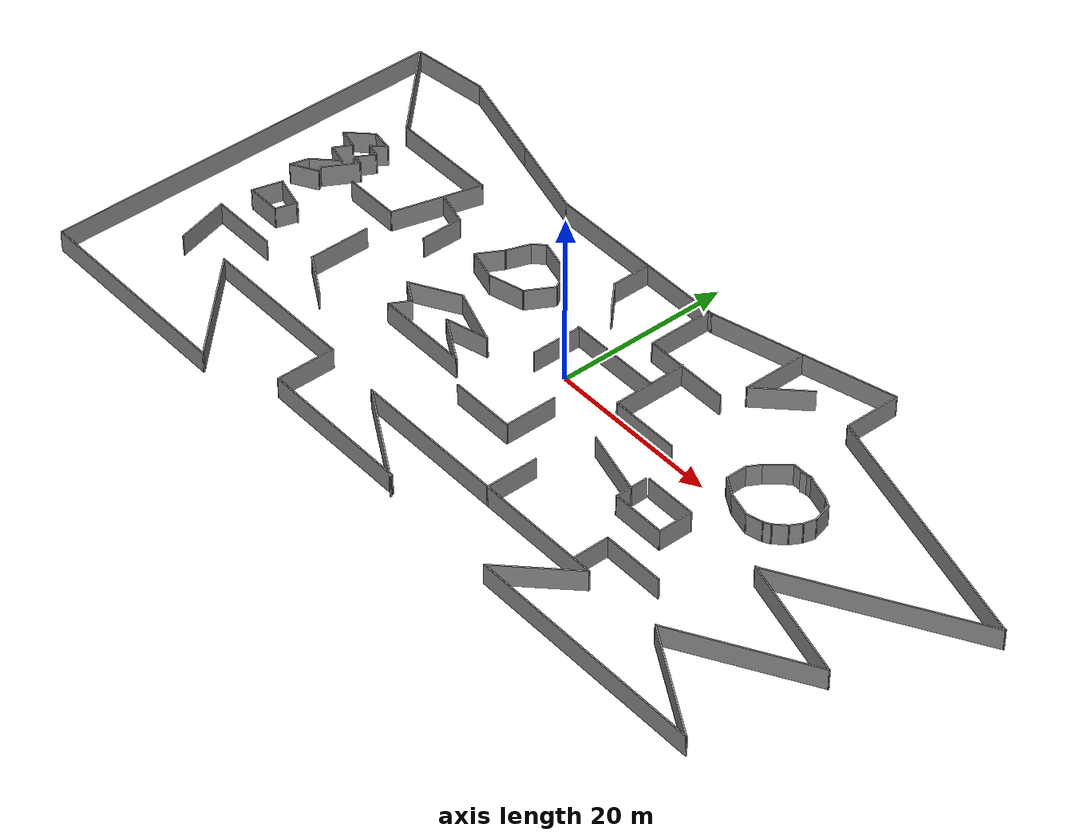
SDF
<?xml version='1.0'?>
<sdf version='1.7'>
  <model name='custommap4'>
    <pose>3.03958 -2.67681 0 0 -0 0</pose>
    <link name='Wall_10'>
      <collision name='Wall_10_Collision'>
        <geometry>
          <box>
            <size>12.5 0.15 2.5</size>
          </box>
        </geometry>
        <pose>0 0 1.25 0 -0 0</pose>
      </collision>
      <visual name='Wall_10_Visual'>
        <pose>0 0 1.25 0 -0 0</pose>
        <geometry>
          <box>
            <size>12.5 0.15 2.5</size>
          </box>
        </geometry>
        <material>
          <script>
            <uri>file://media/materials/scripts/gazebo.material</uri>
            <name>Gazebo/Grey</name>
          </script>
          <ambient>1 1 1 1</ambient>
        </material>
        <meta>
          <layer>0</layer>
        </meta>
      </visual>
      <pose>-6.3228 -17.4231 0 0 -0 2.61799</pose>
    </link>
    <link name='Wall_100'>
      <collision name='Wall_100_Collision'>
        <geometry>
          <box>
            <size>3.27089 0.15 2.5</size>
          </box>
        </geometry>
        <pose>0 0 1.25 0 -0 0</pose>
      </collision>
      <visual name='Wall_100_Visual'>
        <pose>0 0 1.25 0 -0 0</pose>
        <geometry>
          <box>
            <size>3.27089 0.15 2.5</size>
          </box>
        </geometry>
        <material>
          <script>
            <uri>file://media/materials/scripts/gazebo.material</uri>
            <name>Gazebo/Grey</name>
          </script>
          <ambient>1 1 1 1</ambient>
        </material>
        <meta>
          <layer>0</layer>
        </meta>
      </visual>
      <pose>25.8005 9.23702 0 0 -0 2.85212</pose>
    </link>
    <link name='Wall_101'>
      <collision name='Wall_101_Collision'>
        <geometry>
          <box>
            <size>1.25 0.15 2.5</size>
          </box>
        </geometry>
        <pose>0 0 1.25 0 -0 0</pose>
      </collision>
      <visual name='Wall_101_Visual'>
        <pose>0 0 1.25 0 -0 0</pose>
        <geometry>
          <box>
            <size>1.25 0.15 2.5</size>
          </box>
        </geometry>
        <material>
          <script>
            <uri>file://media/materials/scripts/gazebo.material</uri>
            <name>Gazebo/Grey</name>
          </script>
          <ambient>1 1 1 1</ambient>
        </material>
        <meta>
          <layer>0</layer>
        </meta>
      </visual>
      <pose>23.7737 9.60162 0 0 -0 -2.87979</pose>
    </link>
    <link name='Wall_103'>
      <collision name='Wall_103_Collision'>
        <geometry>
          <box>
            <size>6 0.15 2.5</size>
          </box>
        </geometry>
        <pose>0 0 1.25 0 -0 0</pose>
      </collision>
      <visual name='Wall_103_Visual'>
        <pose>0 0 1.25 0 -0 0</pose>
        <geometry>
          <box>
            <size>6 0.15 2.5</size>
          </box>
        </geometry>
        <material>
          <script>
            <uri>file://media/materials/scripts/gazebo.material</uri>
            <name>Gazebo/Grey</name>
          </script>
          <ambient>1 1 1 1</ambient>
        </material>
        <meta>
          <layer>0</layer>
        </meta>
      </visual>
      <pose>0.440583 -4.58212 0 0 -0 -1.5708</pose>
    </link>
    <link name='Wall_104'>
      <collision name='Wall_104_Collision'>
        <geometry>
          <box>
            <size>7.5 0.15 2.5</size>
          </box>
        </geometry>
        <pose>0 0 1.25 0 -0 0</pose>
      </collision>
      <visual name='Wall_104_Visual'>
        <pose>0 0 1.25 0 -0 0</pose>
        <geometry>
          <box>
            <size>7.5 0.15 2.5</size>
          </box>
        </geometry>
        <material>
          <script>
            <uri>file://media/materials/scripts/gazebo.material</uri>
            <name>Gazebo/Grey</name>
          </script>
          <ambient>1 1 1 1</ambient>
        </material>
        <meta>
          <layer>0</layer>
        </meta>
      </visual>
      <pose>-3.23442 -7.50712 0 0 -0 3.14159</pose>
    </link>
    <link name='Wall_106'>
      <collision name='Wall_106_Collision'>
        <geometry>
          <box>
            <size>3.75 0.15 2.5</size>
          </box>
        </geometry>
        <pose>0 0 1.25 0 -0 0</pose>
      </collision>
      <visual name='Wall_106_Visual'>
        <pose>0 0 1.25 0 -0 0</pose>
        <geometry>
          <box>
            <size>3.75 0.15 2.5</size>
          </box>
        </geometry>
        <material>
          <script>
            <uri>file://media/materials/scripts/gazebo.material</uri>
            <name>Gazebo/Grey</name>
          </script>
          <ambient>1 1 1 1</ambient>
        </material>
        <meta>
          <layer>0</layer>
        </meta>
      </visual>
      <pose>14.5378 -4.10279 0 0 -0 -1.5708</pose>
    </link>
    <link name='Wall_107'>
      <collision name='Wall_107_Collision'>
        <geometry>
          <box>
            <size>6.25 0.15 2.5</size>
          </box>
        </geometry>
        <pose>0 0 1.25 0 -0 0</pose>
      </collision>
      <visual name='Wall_107_Visual'>
        <pose>0 0 1.25 0 -0 0</pose>
        <geometry>
          <box>
            <size>6.25 0.15 2.5</size>
          </box>
        </geometry>
        <material>
          <script>
            <uri>file://media/materials/scripts/gazebo.material</uri>
            <name>Gazebo/Grey</name>
          </script>
          <ambient>1 1 1 1</ambient>
        </material>
        <meta>
          <layer>0</layer>
        </meta>
      </visual>
      <pose>17.5878 -5.90279 0 0 -0 0</pose>
    </link>
    <link name='Wall_108'>
      <collision name='Wall_108_Collision'>
        <geometry>
          <box>
            <size>4 0.15 2.5</size>
          </box>
        </geometry>
        <pose>0 0 1.25 0 -0 0</pose>
      </collision>
      <visual name='Wall_108_Visual'>
        <pose>0 0 1.25 0 -0 0</pose>
        <geometry>
          <box>
            <size>4 0.15 2.5</size>
          </box>
        </geometry>
        <material>
          <script>
            <uri>file://media/materials/scripts/gazebo.material</uri>
            <name>Gazebo/Grey</name>
          </script>
          <ambient>1 1 1 1</ambient>
        </material>
        <meta>
          <layer>0</layer>
        </meta>
      </visual>
      <pose>20.6378 -3.97779 0 0 -0 1.5708</pose>
    </link>
    <link name='Wall_109'>
      <collision name='Wall_109_Collision'>
        <geometry>
          <box>
            <size>6 0.15 2.5</size>
          </box>
        </geometry>
        <pose>0 0 1.25 0 -0 0</pose>
      </collision>
      <visual name='Wall_109_Visual'>
        <pose>0 0 1.25 0 -0 0</pose>
        <geometry>
          <box>
            <size>6 0.15 2.5</size>
          </box>
        </geometry>
        <material>
          <script>
            <uri>file://media/materials/scripts/gazebo.material</uri>
            <name>Gazebo/Grey</name>
          </script>
          <ambient>1 1 1 1</ambient>
        </material>
        <meta>
          <layer>0</layer>
        </meta>
      </visual>
      <pose>17.7128 -2.05279 0 0 -0 3.14159</pose>
    </link>
    <link name='Wall_11'>
      <collision name='Wall_11_Collision'>
        <geometry>
          <box>
            <size>32.25 0.15 2.5</size>
          </box>
        </geometry>
        <pose>0 0 1.25 0 -0 0</pose>
      </collision>
      <visual name='Wall_11_Visual'>
        <pose>0 0 1.25 0 -0 0</pose>
        <geometry>
          <box>
            <size>32.25 0.15 2.5</size>
          </box>
        </geometry>
        <material>
          <script>
            <uri>file://media/materials/scripts/gazebo.material</uri>
            <name>Gazebo/Grey</name>
          </script>
          <ambient>1 1 1 1</ambient>
        </material>
        <meta>
          <layer>0</layer>
        </meta>
      </visual>
      <pose>4.3795 -14.3356 0 0 -0 0</pose>
    </link>
    <link name='Wall_111'>
      <collision name='Wall_111_Collision'>
        <geometry>
          <box>
            <size>7.75 0.15 2.5</size>
          </box>
        </geometry>
        <pose>0 0 1.25 0 -0 0</pose>
      </collision>
      <visual name='Wall_111_Visual'>
        <pose>0 0 1.25 0 -0 0</pose>
        <geometry>
          <box>
            <size>7.75 0.15 2.5</size>
          </box>
        </geometry>
        <material>
          <script>
            <uri>file://media/materials/scripts/gazebo.material</uri>
            <name>Gazebo/Grey</name>
          </script>
          <ambient>1 1 1 1</ambient>
        </material>
        <meta>
          <layer>0</layer>
        </meta>
      </visual>
      <pose>10.8907 -3.17869 0 0 -0 -0.261799</pose>
    </link>
    <link name='Wall_113'>
      <collision name='Wall_113_Collision'>
        <geometry>
          <box>
            <size>7.25 0.15 2.5</size>
          </box>
        </geometry>
        <pose>0 0 1.25 0 -0 0</pose>
      </collision>
      <visual name='Wall_113_Visual'>
        <pose>0 0 1.25 0 -0 0</pose>
        <geometry>
          <box>
            <size>7.25 0.15 2.5</size>
          </box>
        </geometry>
        <material>
          <script>
            <uri>file://media/materials/scripts/gazebo.material</uri>
            <name>Gazebo/Grey</name>
          </script>
          <ambient>1 1 1 1</ambient>
        </material>
        <meta>
          <layer>0</layer>
        </meta>
      </visual>
      <pose>21.7491 -10.1585 0 0 -0 3.14159</pose>
    </link>
    <link name='Wall_114'>
      <collision name='Wall_114_Collision'>
        <geometry>
          <box>
            <size>4.25 0.15 2.5</size>
          </box>
        </geometry>
        <pose>0 0 1.25 0 -0 0</pose>
      </collision>
      <visual name='Wall_114_Visual'>
        <pose>0 0 1.25 0 -0 0</pose>
        <geometry>
          <box>
            <size>4.25 0.15 2.5</size>
          </box>
        </geometry>
        <material>
          <script>
            <uri>file://media/materials/scripts/gazebo.material</uri>
            <name>Gazebo/Grey</name>
          </script>
          <ambient>1 1 1 1</ambient>
        </material>
        <meta>
          <layer>0</layer>
        </meta>
      </visual>
      <pose>18.1991 -12.2085 0 0 -0 -1.5708</pose>
    </link>
    <link name='Wall_116'>
      <collision name='Wall_116_Collision'>
        <geometry>
          <box>
            <size>7.25 0.15 2.5</size>
          </box>
        </geometry>
        <pose>0 0 1.25 0 -0 0</pose>
      </collision>
      <visual name='Wall_116_Visual'>
        <pose>0 0 1.25 0 -0 0</pose>
        <geometry>
          <box>
            <size>7.25 0.15 2.5</size>
          </box>
        </geometry>
        <material>
          <script>
            <uri>file://media/materials/scripts/gazebo.material</uri>
            <name>Gazebo/Grey</name>
          </script>
          <ambient>1 1 1 1</ambient>
        </material>
        <meta>
          <layer>0</layer>
        </meta>
      </visual>
      <pose>11.2018 17.0687 0 0 -0 -1.5708</pose>
    </link>
    <link name='Wall_117'>
      <collision name='Wall_117_Collision'>
        <geometry>
          <box>
            <size>6.75 0.15 2.5</size>
          </box>
        </geometry>
        <pose>0 0 1.25 0 -0 0</pose>
      </collision>
      <visual name='Wall_117_Visual'>
        <pose>0 0 1.25 0 -0 0</pose>
        <geometry>
          <box>
            <size>6.75 0.15 2.5</size>
          </box>
        </geometry>
        <material>
          <script>
            <uri>file://media/materials/scripts/gazebo.material</uri>
            <name>Gazebo/Grey</name>
          </script>
          <ambient>1 1 1 1</ambient>
        </material>
        <meta>
          <layer>0</layer>
        </meta>
      </visual>
      <pose>13.5353 15.8522 0 0 -0 0.785398</pose>
    </link>
    <link name='Wall_119'>
      <collision name='Wall_119_Collision'>
        <geometry>
          <box>
            <size>4.5 0.15 2.5</size>
          </box>
        </geometry>
        <pose>0 0 1.25 0 -0 0</pose>
      </collision>
      <visual name='Wall_119_Visual'>
        <pose>0 0 1.25 0 -0 0</pose>
        <geometry>
          <box>
            <size>4.5 0.15 2.5</size>
          </box>
        </geometry>
        <material>
          <script>
            <uri>file://media/materials/scripts/gazebo.material</uri>
            <name>Gazebo/Grey</name>
          </script>
          <ambient>1 1 1 1</ambient>
        </material>
        <meta>
          <layer>0</layer>
        </meta>
      </visual>
      <pose>-8.49127 15.861 0 0 -0 -1.5708</pose>
    </link>
    <link name='Wall_12'>
      <collision name='Wall_12_Collision'>
        <geometry>
          <box>
            <size>9.75 0.15 2.5</size>
          </box>
        </geometry>
        <pose>0 0 1.25 0 -0 0</pose>
      </collision>
      <visual name='Wall_12_Visual'>
        <pose>0 0 1.25 0 -0 0</pose>
        <geometry>
          <box>
            <size>9.75 0.15 2.5</size>
          </box>
        </geometry>
        <material>
          <script>
            <uri>file://media/materials/scripts/gazebo.material</uri>
            <name>Gazebo/Grey</name>
          </script>
          <ambient>1 1 1 1</ambient>
        </material>
        <meta>
          <layer>0</layer>
        </meta>
      </visual>
      <pose>17.0354 -17.7297 0 0 -0 -2.35619</pose>
    </link>
    <link name='Wall_120'>
      <collision name='Wall_120_Collision'>
        <geometry>
          <box>
            <size>4 0.15 2.5</size>
          </box>
        </geometry>
        <pose>0 0 1.25 0 -0 0</pose>
      </collision>
      <visual name='Wall_120_Visual'>
        <pose>0 0 1.25 0 -0 0</pose>
        <geometry>
          <box>
            <size>4 0.15 2.5</size>
          </box>
        </geometry>
        <material>
          <script>
            <uri>file://media/materials/scripts/gazebo.material</uri>
            <name>Gazebo/Grey</name>
          </script>
          <ambient>1 1 1 1</ambient>
        </material>
        <meta>
          <layer>0</layer>
        </meta>
      </visual>
      <pose>-7.13009 12.3248 0 0 -0 -0.785398</pose>
    </link>
    <link name='Wall_13'>
      <collision name='Wall_13_Collision'>
        <geometry>
          <box>
            <size>28 0.15 2.5</size>
          </box>
        </geometry>
        <pose>0 0 1.25 0 -0 0</pose>
      </collision>
      <visual name='Wall_13_Visual'>
        <pose>0 0 1.25 0 -0 0</pose>
        <geometry>
          <box>
            <size>28 0.15 2.5</size>
          </box>
        </geometry>
        <material>
          <script>
            <uri>file://media/materials/scripts/gazebo.material</uri>
            <name>Gazebo/Grey</name>
          </script>
          <ambient>1 1 1 1</ambient>
        </material>
        <meta>
          <layer>0</layer>
        </meta>
      </visual>
      <pose>27.5663 -21.1238 0 0 -0 0</pose>
    </link>
    <link name='Wall_14'>
      <collision name='Wall_14_Collision'>
        <geometry>
          <box>
            <size>14 0.15 2.5</size>
          </box>
        </geometry>
        <pose>0 0 1.25 0 -0 0</pose>
      </collision>
      <visual name='Wall_14_Visual'>
        <pose>0 0 1.25 0 -0 0</pose>
        <geometry>
          <box>
            <size>14 0.15 2.5</size>
          </box>
        </geometry>
        <material>
          <script>
            <uri>file://media/materials/scripts/gazebo.material</uri>
            <name>Gazebo/Grey</name>
          </script>
          <ambient>1 1 1 1</ambient>
        </material>
        <meta>
          <layer>0</layer>
        </meta>
      </visual>
      <pose>35.494 -17.6613 0 0 -0 2.61799</pose>
    </link>
    <link name='Wall_15'>
      <collision name='Wall_15_Collision'>
        <geometry>
          <box>
            <size>16.5 0.15 2.5</size>
          </box>
        </geometry>
        <pose>0 0 1.25 0 -0 0</pose>
      </collision>
      <visual name='Wall_15_Visual'>
        <pose>0 0 1.25 0 -0 0</pose>
        <geometry>
          <box>
            <size>16.5 0.15 2.5</size>
          </box>
        </geometry>
        <material>
          <script>
            <uri>file://media/materials/scripts/gazebo.material</uri>
            <name>Gazebo/Grey</name>
          </script>
          <ambient>1 1 1 1</ambient>
        </material>
        <meta>
          <layer>0</layer>
        </meta>
      </visual>
      <pose>36.5766 -10.1113 0 0 -0 0.523599</pose>
    </link>
    <link name='Wall_16'>
      <collision name='Wall_16_Collision'>
        <geometry>
          <box>
            <size>14.5 0.15 2.5</size>
          </box>
        </geometry>
        <pose>0 0 1.25 0 -0 0</pose>
      </collision>
      <visual name='Wall_16_Visual'>
        <pose>0 0 1.25 0 -0 0</pose>
        <geometry>
          <box>
            <size>14.5 0.15 2.5</size>
          </box>
        </geometry>
        <material>
          <script>
            <uri>file://media/materials/scripts/gazebo.material</uri>
            <name>Gazebo/Grey</name>
          </script>
          <ambient>1 1 1 1</ambient>
        </material>
        <meta>
          <layer>0</layer>
        </meta>
      </visual>
      <pose>36.7258 -4.16677 0 0 -0 2.87979</pose>
    </link>
    <link name='Wall_17'>
      <collision name='Wall_17_Collision'>
        <geometry>
          <box>
            <size>23.75 0.15 2.5</size>
          </box>
        </geometry>
        <pose>0 0 1.25 0 -0 0</pose>
      </collision>
      <visual name='Wall_17_Visual'>
        <pose>0 0 1.25 0 -0 0</pose>
        <geometry>
          <box>
            <size>23.75 0.15 2.5</size>
          </box>
        </geometry>
        <material>
          <script>
            <uri>file://media/materials/scripts/gazebo.material</uri>
            <name>Gazebo/Grey</name>
          </script>
          <ambient>1 1 1 1</ambient>
        </material>
        <meta>
          <layer>0</layer>
        </meta>
      </visual>
      <pose>40.0144 3.59025 0 0 -0 0.523599</pose>
    </link>
    <link name='Wall_18'>
      <collision name='Wall_18_Collision'>
        <geometry>
          <box>
            <size>30 0.15 2.5</size>
          </box>
        </geometry>
        <pose>0 0 1.25 0 -0 0</pose>
      </collision>
      <visual name='Wall_18_Visual'>
        <pose>0 0 1.25 0 -0 0</pose>
        <geometry>
          <box>
            <size>30 0.15 2.5</size>
          </box>
        </geometry>
        <material>
          <script>
            <uri>file://media/materials/scripts/gazebo.material</uri>
            <name>Gazebo/Grey</name>
          </script>
          <ambient>1 1 1 1</ambient>
        </material>
        <meta>
          <layer>0</layer>
        </meta>
      </visual>
      <pose>35.8171 13.3531 0 0 -0 2.87979</pose>
    </link>
    <link name='Wall_19'>
      <collision name='Wall_19_Collision'>
        <geometry>
          <box>
            <size>6.5 0.15 2.5</size>
          </box>
        </geometry>
        <pose>0 0 1.25 0 -0 0</pose>
      </collision>
      <visual name='Wall_19_Visual'>
        <pose>0 0 1.25 0 -0 0</pose>
        <geometry>
          <box>
            <size>6.5 0.15 2.5</size>
          </box>
        </geometry>
        <material>
          <script>
            <uri>file://media/materials/scripts/gazebo.material</uri>
            <name>Gazebo/Grey</name>
          </script>
          <ambient>1 1 1 1</ambient>
        </material>
        <meta>
          <layer>0</layer>
        </meta>
      </visual>
      <pose>21.4006 20.391 0 0 -0 1.5708</pose>
    </link>
    <link name='Wall_20'>
      <collision name='Wall_20_Collision'>
        <geometry>
          <box>
            <size>21.25 0.15 2.5</size>
          </box>
        </geometry>
        <pose>0 0 1.25 0 -0 0</pose>
      </collision>
      <visual name='Wall_20_Visual'>
        <pose>0 0 1.25 0 -0 0</pose>
        <geometry>
          <box>
            <size>21.25 0.15 2.5</size>
          </box>
        </geometry>
        <material>
          <script>
            <uri>file://media/materials/scripts/gazebo.material</uri>
            <name>Gazebo/Grey</name>
          </script>
          <ambient>1 1 1 1</ambient>
        </material>
        <meta>
          <layer>0</layer>
        </meta>
      </visual>
      <pose>11.2101 20.8355 0 0 -0 -2.87979</pose>
    </link>
    <link name='Wall_21'>
      <collision name='Wall_21_Collision'>
        <geometry>
          <box>
            <size>22.25 0.15 2.5</size>
          </box>
        </geometry>
        <pose>0 0 1.25 0 -0 0</pose>
      </collision>
      <visual name='Wall_21_Visual'>
        <pose>0 0 1.25 0 -0 0</pose>
        <geometry>
          <box>
            <size>22.25 0.15 2.5</size>
          </box>
        </geometry>
        <material>
          <script>
            <uri>file://media/materials/scripts/gazebo.material</uri>
            <name>Gazebo/Grey</name>
          </script>
          <ambient>1 1 1 1</ambient>
        </material>
        <meta>
          <layer>0</layer>
        </meta>
      </visual>
      <pose>-10.0304 18.1049 0 0 -0 3.14159</pose>
    </link>
    <link name='Wall_22'>
      <collision name='Wall_22_Collision'>
        <geometry>
          <box>
            <size>10 0.15 2.5</size>
          </box>
        </geometry>
        <pose>0 0 1.25 0 -0 0</pose>
      </collision>
      <visual name='Wall_22_Visual'>
        <pose>0 0 1.25 0 -0 0</pose>
        <geometry>
          <box>
            <size>10 0.15 2.5</size>
          </box>
        </geometry>
        <material>
          <script>
            <uri>file://media/materials/scripts/gazebo.material</uri>
            <name>Gazebo/Grey</name>
          </script>
          <ambient>1 1 1 1</ambient>
        </material>
        <meta>
          <layer>0</layer>
        </meta>
      </visual>
      <pose>-25.8376 19.3796 0 0 -0 2.87979</pose>
    </link>
    <link name='Wall_23'>
      <collision name='Wall_23_Collision'>
        <geometry>
          <box>
            <size>11.5 0.15 2.5</size>
          </box>
        </geometry>
        <pose>0 0 1.25 0 -0 0</pose>
      </collision>
      <visual name='Wall_23_Visual'>
        <pose>0 0 1.25 0 -0 0</pose>
        <geometry>
          <box>
            <size>11.5 0.15 2.5</size>
          </box>
        </geometry>
        <material>
          <script>
            <uri>file://media/materials/scripts/gazebo.material</uri>
            <name>Gazebo/Grey</name>
          </script>
          <ambient>1 1 1 1</ambient>
        </material>
        <meta>
          <layer>0</layer>
        </meta>
      </visual>
      <pose>-36.0764 22.1231 0 0 -0 2.87979</pose>
    </link>
    <link name='Wall_24'>
      <collision name='Wall_24_Collision'>
        <geometry>
          <box>
            <size>8.88754 0.15 2.5</size>
          </box>
        </geometry>
        <pose>0 0 1.25 0 -0 0</pose>
      </collision>
      <visual name='Wall_24_Visual'>
        <pose>0 0 1.25 0 -0 0</pose>
        <geometry>
          <box>
            <size>8.88754 0.15 2.5</size>
          </box>
        </geometry>
        <material>
          <script>
            <uri>file://media/materials/scripts/gazebo.material</uri>
            <name>Gazebo/Grey</name>
          </script>
          <ambient>1 1 1 1</ambient>
        </material>
        <meta>
          <layer>0</layer>
        </meta>
      </visual>
      <pose>-45.894 23.0571 0 0 -0 -3.01888</pose>
    </link>
    <link name='Wall_25'>
      <collision name='Wall_25_Collision'>
        <geometry>
          <box>
            <size>13 0.15 2.5</size>
          </box>
        </geometry>
        <pose>0 0 1.25 0 -0 0</pose>
      </collision>
      <visual name='Wall_25_Visual'>
        <pose>0 0 1.25 0 -0 0</pose>
        <geometry>
          <box>
            <size>13 0.15 2.5</size>
          </box>
        </geometry>
        <material>
          <script>
            <uri>file://media/materials/scripts/gazebo.material</uri>
            <name>Gazebo/Grey</name>
          </script>
          <ambient>1 1 1 1</ambient>
        </material>
        <meta>
          <layer>0</layer>
        </meta>
      </visual>
      <pose>-45.6867 17.9792 0 0 -0 -0.785398</pose>
    </link>
    <link name='Wall_26'>
      <collision name='Wall_26_Collision'>
        <geometry>
          <box>
            <size>12.5 0.15 2.5</size>
          </box>
        </geometry>
        <pose>0 0 1.25 0 -0 0</pose>
      </collision>
      <visual name='Wall_26_Visual'>
        <pose>0 0 1.25 0 -0 0</pose>
        <geometry>
          <box>
            <size>12.5 0.15 2.5</size>
          </box>
        </geometry>
        <material>
          <script>
            <uri>file://media/materials/scripts/gazebo.material</uri>
            <name>Gazebo/Grey</name>
          </script>
          <ambient>1 1 1 1</ambient>
        </material>
        <meta>
          <layer>0</layer>
        </meta>
      </visual>
      <pose>-34.9686 13.436 0 0 -0 0</pose>
    </link>
    <link name='Wall_27'>
      <collision name='Wall_27_Collision'>
        <geometry>
          <box>
            <size>10.25 0.15 2.5</size>
          </box>
        </geometry>
        <pose>0 0 1.25 0 -0 0</pose>
      </collision>
      <visual name='Wall_27_Visual'>
        <pose>0 0 1.25 0 -0 0</pose>
        <geometry>
          <box>
            <size>10.25 0.15 2.5</size>
          </box>
        </geometry>
        <material>
          <script>
            <uri>file://media/materials/scripts/gazebo.material</uri>
            <name>Gazebo/Grey</name>
          </script>
          <ambient>1 1 1 1</ambient>
        </material>
        <meta>
          <layer>0</layer>
        </meta>
      </visual>
      <pose>-30.1006 8.55808 0 0 -0 -1.8326</pose>
    </link>
    <link name='Wall_28'>
      <collision name='Wall_28_Collision'>
        <geometry>
          <box>
            <size>6.5 0.15 2.5</size>
          </box>
        </geometry>
        <pose>0 0 1.25 0 -0 0</pose>
      </collision>
      <visual name='Wall_28_Visual'>
        <pose>0 0 1.25 0 -0 0</pose>
        <geometry>
          <box>
            <size>6.5 0.15 2.5</size>
          </box>
        </geometry>
        <material>
          <script>
            <uri>file://media/materials/scripts/gazebo.material</uri>
            <name>Gazebo/Grey</name>
          </script>
          <ambient>1 1 1 1</ambient>
        </material>
        <meta>
          <layer>0</layer>
        </meta>
      </visual>
      <pose>-34.5826 3.68016 0 0 -0 3.14159</pose>
    </link>
    <link name='Wall_3'>
      <collision name='Wall_3_Collision'>
        <geometry>
          <box>
            <size>46.25 0.15 2.5</size>
          </box>
        </geometry>
        <pose>0 0 1.25 0 -0 0</pose>
      </collision>
      <visual name='Wall_3_Visual'>
        <pose>0 0 1.25 0 -0 0</pose>
        <geometry>
          <box>
            <size>46.25 0.15 2.5</size>
          </box>
        </geometry>
        <material>
          <script>
            <uri>file://media/materials/scripts/gazebo.material</uri>
            <name>Gazebo/Grey</name>
          </script>
          <ambient>1 1 1 1</ambient>
        </material>
        <meta>
          <layer>0</layer>
        </meta>
      </visual>
      <pose>-50.2299 -0.527672 0 0 -0 -1.5708</pose>
    </link>
    <link name='Wall_30'>
      <collision name='Wall_30_Collision'>
        <geometry>
          <box>
            <size>3.5 0.15 2.5</size>
          </box>
        </geometry>
        <pose>0 0 1.25 0 -0 0</pose>
      </collision>
      <visual name='Wall_30_Visual'>
        <pose>0 0 1.25 0 -0 0</pose>
        <geometry>
          <box>
            <size>3.5 0.15 2.5</size>
          </box>
        </geometry>
        <material>
          <script>
            <uri>file://media/materials/scripts/gazebo.material</uri>
            <name>Gazebo/Grey</name>
          </script>
          <ambient>1 1 1 1</ambient>
        </material>
        <meta>
          <layer>0</layer>
        </meta>
      </visual>
      <pose>-42.7705 -3.34404 0 0 -0 -1.8326</pose>
    </link>
    <link name='Wall_31'>
      <collision name='Wall_31_Collision'>
        <geometry>
          <box>
            <size>4 0.15 2.5</size>
          </box>
        </geometry>
        <pose>0 0 1.25 0 -0 0</pose>
      </collision>
      <visual name='Wall_31_Visual'>
        <pose>0 0 1.25 0 -0 0</pose>
        <geometry>
          <box>
            <size>4 0.15 2.5</size>
          </box>
        </geometry>
        <material>
          <script>
            <uri>file://media/materials/scripts/gazebo.material</uri>
            <name>Gazebo/Grey</name>
          </script>
          <ambient>1 1 1 1</ambient>
        </material>
        <meta>
          <layer>0</layer>
        </meta>
      </visual>
      <pose>-41.279 -4.96197 0 0 -0 0</pose>
    </link>
    <link name='Wall_32'>
      <collision name='Wall_32_Collision'>
        <geometry>
          <box>
            <size>2.53049 0.15 2.5</size>
          </box>
        </geometry>
        <pose>0 0 1.25 0 -0 0</pose>
      </collision>
      <visual name='Wall_32_Visual'>
        <pose>0 0 1.25 0 -0 0</pose>
        <geometry>
          <box>
            <size>2.53049 0.15 2.5</size>
          </box>
        </geometry>
        <material>
          <script>
            <uri>file://media/materials/scripts/gazebo.material</uri>
            <name>Gazebo/Grey</name>
          </script>
          <ambient>1 1 1 1</ambient>
        </material>
        <meta>
          <layer>0</layer>
        </meta>
      </visual>
      <pose>-39.0106 -3.82233 0 0 -0 1.27814</pose>
    </link>
    <link name='Wall_33'>
      <collision name='Wall_33_Collision'>
        <geometry>
          <box>
            <size>4 0.15 2.5</size>
          </box>
        </geometry>
        <pose>0 0 1.25 0 -0 0</pose>
      </collision>
      <visual name='Wall_33_Visual'>
        <pose>0 0 1.25 0 -0 0</pose>
        <geometry>
          <box>
            <size>4 0.15 2.5</size>
          </box>
        </geometry>
        <material>
          <script>
            <uri>file://media/materials/scripts/gazebo.material</uri>
            <name>Gazebo/Grey</name>
          </script>
          <ambient>1 1 1 1</ambient>
        </material>
        <meta>
          <layer>0</layer>
        </meta>
      </visual>
      <pose>-40.4452 -2.26584 0 0 -0 2.87979</pose>
    </link>
    <link name='Wall_35'>
      <collision name='Wall_35_Collision'>
        <geometry>
          <box>
            <size>6 0.15 2.5</size>
          </box>
        </geometry>
        <pose>0 0 1.25 0 -0 0</pose>
      </collision>
      <visual name='Wall_35_Visual'>
        <pose>0 0 1.25 0 -0 0</pose>
        <geometry>
          <box>
            <size>6 0.15 2.5</size>
          </box>
        </geometry>
        <material>
          <script>
            <uri>file://media/materials/scripts/gazebo.material</uri>
            <name>Gazebo/Grey</name>
          </script>
          <ambient>1 1 1 1</ambient>
        </material>
        <meta>
          <layer>0</layer>
        </meta>
      </visual>
      <pose>-19.3197 -0.340644 0 0 -0 -2.61799</pose>
    </link>
    <link name='Wall_36'>
      <collision name='Wall_36_Collision'>
        <geometry>
          <box>
            <size>3 0.15 2.5</size>
          </box>
        </geometry>
        <pose>0 0 1.25 0 -0 0</pose>
      </collision>
      <visual name='Wall_36_Visual'>
        <pose>0 0 1.25 0 -0 0</pose>
        <geometry>
          <box>
            <size>3 0.15 2.5</size>
          </box>
        </geometry>
        <material>
          <script>
            <uri>file://media/materials/scripts/gazebo.material</uri>
            <name>Gazebo/Grey</name>
          </script>
          <ambient>1 1 1 1</ambient>
        </material>
        <meta>
          <layer>0</layer>
        </meta>
      </visual>
      <pose>-20.6187 -2.51564 0 0 -0 -0.523599</pose>
    </link>
    <link name='Wall_37'>
      <collision name='Wall_37_Collision'>
        <geometry>
          <box>
            <size>2.5 0.15 2.5</size>
          </box>
        </geometry>
        <pose>0 0 1.25 0 -0 0</pose>
      </collision>
      <visual name='Wall_37_Visual'>
        <pose>0 0 1.25 0 -0 0</pose>
        <geometry>
          <box>
            <size>2.5 0.15 2.5</size>
          </box>
        </geometry>
        <material>
          <script>
            <uri>file://media/materials/scripts/gazebo.material</uri>
            <name>Gazebo/Grey</name>
          </script>
          <ambient>1 1 1 1</ambient>
        </material>
        <meta>
          <layer>0</layer>
        </meta>
      </visual>
      <pose>-19.9721 -4.24572 0 0 -0 -2.0944</pose>
    </link>
    <link name='Wall_38'>
      <collision name='Wall_38_Collision'>
        <geometry>
          <box>
            <size>10.75 0.15 2.5</size>
          </box>
        </geometry>
        <pose>0 0 1.25 0 -0 0</pose>
      </collision>
      <visual name='Wall_38_Visual'>
        <pose>0 0 1.25 0 -0 0</pose>
        <geometry>
          <box>
            <size>10.75 0.15 2.5</size>
          </box>
        </geometry>
        <material>
          <script>
            <uri>file://media/materials/scripts/gazebo.material</uri>
            <name>Gazebo/Grey</name>
          </script>
          <ambient>1 1 1 1</ambient>
        </material>
        <meta>
          <layer>0</layer>
        </meta>
      </visual>
      <pose>-15.2596 -5.2633 0 0 -0 0</pose>
    </link>
    <link name='Wall_39'>
      <collision name='Wall_39_Collision'>
        <geometry>
          <box>
            <size>6 0.15 2.5</size>
          </box>
        </geometry>
        <pose>0 0 1.25 0 -0 0</pose>
      </collision>
      <visual name='Wall_39_Visual'>
        <pose>0 0 1.25 0 -0 0</pose>
        <geometry>
          <box>
            <size>6 0.15 2.5</size>
          </box>
        </geometry>
        <material>
          <script>
            <uri>file://media/materials/scripts/gazebo.material</uri>
            <name>Gazebo/Grey</name>
          </script>
          <ambient>1 1 1 1</ambient>
        </material>
        <meta>
          <layer>0</layer>
        </meta>
      </visual>
      <pose>-12.4928 -3.8008 0 0 -0 2.61799</pose>
    </link>
    <link name='Wall_4'>
      <collision name='Wall_4_Collision'>
        <geometry>
          <box>
            <size>24 0.15 2.5</size>
          </box>
        </geometry>
        <pose>0 0 1.25 0 -0 0</pose>
      </collision>
      <visual name='Wall_4_Visual'>
        <pose>0 0 1.25 0 -0 0</pose>
        <geometry>
          <box>
            <size>24 0.15 2.5</size>
          </box>
        </geometry>
        <material>
          <script>
            <uri>file://media/materials/scripts/gazebo.material</uri>
            <name>Gazebo/Grey</name>
          </script>
          <ambient>1 1 1 1</ambient>
        </material>
        <meta>
          <layer>0</layer>
        </meta>
      </visual>
      <pose>-38.3049 -23.5777 0 0 -0 0</pose>
    </link>
    <link name='Wall_40'>
      <collision name='Wall_40_Collision'>
        <geometry>
          <box>
            <size>5 0.15 2.5</size>
          </box>
        </geometry>
        <pose>0 0 1.25 0 -0 0</pose>
      </collision>
      <visual name='Wall_40_Visual'>
        <pose>0 0 1.25 0 -0 0</pose>
        <geometry>
          <box>
            <size>5 0.15 2.5</size>
          </box>
        </geometry>
        <material>
          <script>
            <uri>file://media/materials/scripts/gazebo.material</uri>
            <name>Gazebo/Grey</name>
          </script>
          <ambient>1 1 1 1</ambient>
        </material>
        <meta>
          <layer>0</layer>
        </meta>
      </visual>
      <pose>-12.6835 -1.71067 0 0 -0 0.261799</pose>
    </link>
    <link name='Wall_41'>
      <collision name='Wall_41_Collision'>
        <geometry>
          <box>
            <size>6.96211 0.15 2.5</size>
          </box>
        </geometry>
        <pose>0 0 1.25 0 -0 0</pose>
      </collision>
      <visual name='Wall_41_Visual'>
        <pose>0 0 1.25 0 -0 0</pose>
        <geometry>
          <box>
            <size>6.96211 0.15 2.5</size>
          </box>
        </geometry>
        <material>
          <script>
            <uri>file://media/materials/scripts/gazebo.material</uri>
            <name>Gazebo/Grey</name>
          </script>
          <ambient>1 1 1 1</ambient>
        </material>
        <meta>
          <layer>0</layer>
        </meta>
      </visual>
      <pose>-13.5639 0.019412 0 0 -0 2.81198</pose>
    </link>
    <link name='Wall_43'>
      <collision name='Wall_43_Collision'>
        <geometry>
          <box>
            <size>7 0.15 2.5</size>
          </box>
        </geometry>
        <pose>0 0 1.25 0 -0 0</pose>
      </collision>
      <visual name='Wall_43_Visual'>
        <pose>0 0 1.25 0 -0 0</pose>
        <geometry>
          <box>
            <size>7 0.15 2.5</size>
          </box>
        </geometry>
        <material>
          <script>
            <uri>file://media/materials/scripts/gazebo.material</uri>
            <name>Gazebo/Grey</name>
          </script>
          <ambient>1 1 1 1</ambient>
        </material>
        <meta>
          <layer>0</layer>
        </meta>
      </visual>
      <pose>-30.945 -3.27959 0 0 -0 -1.5708</pose>
    </link>
    <link name='Wall_44'>
      <collision name='Wall_44_Collision'>
        <geometry>
          <box>
            <size>5.25 0.15 2.5</size>
          </box>
        </geometry>
        <pose>0 0 1.25 0 -0 0</pose>
      </collision>
      <visual name='Wall_44_Visual'>
        <pose>0 0 1.25 0 -0 0</pose>
        <geometry>
          <box>
            <size>5.25 0.15 2.5</size>
          </box>
        </geometry>
        <material>
          <script>
            <uri>file://media/materials/scripts/gazebo.material</uri>
            <name>Gazebo/Grey</name>
          </script>
          <ambient>1 1 1 1</ambient>
        </material>
        <meta>
          <layer>0</layer>
        </meta>
      </visual>
      <pose>-28.7367 -7.97959 0 0 -0 -0.523599</pose>
    </link>
    <link name='Wall_46'>
      <collision name='Wall_46_Collision'>
        <geometry>
          <box>
            <size>3.25 0.15 2.5</size>
          </box>
        </geometry>
        <pose>0 0 1.25 0 -0 0</pose>
      </collision>
      <visual name='Wall_46_Visual'>
        <pose>0 0 1.25 0 -0 0</pose>
        <geometry>
          <box>
            <size>3.25 0.15 2.5</size>
          </box>
        </geometry>
        <material>
          <script>
            <uri>file://media/materials/scripts/gazebo.material</uri>
            <name>Gazebo/Grey</name>
          </script>
          <ambient>1 1 1 1</ambient>
        </material>
        <meta>
          <layer>0</layer>
        </meta>
      </visual>
      <pose>-20.1654 7.34698 0 0 -0 -2.0944</pose>
    </link>
    <link name='Wall_47'>
      <collision name='Wall_47_Collision'>
        <geometry>
          <box>
            <size>3.75 0.15 2.5</size>
          </box>
        </geometry>
        <pose>0 0 1.25 0 -0 0</pose>
      </collision>
      <visual name='Wall_47_Visual'>
        <pose>0 0 1.25 0 -0 0</pose>
        <geometry>
          <box>
            <size>3.75 0.15 2.5</size>
          </box>
        </geometry>
        <material>
          <script>
            <uri>file://media/materials/scripts/gazebo.material</uri>
            <name>Gazebo/Grey</name>
          </script>
          <ambient>1 1 1 1</ambient>
        </material>
        <meta>
          <layer>0</layer>
        </meta>
      </visual>
      <pose>-19.2018 5.53877 0 0 -0 -0.261799</pose>
    </link>
    <link name='Wall_48'>
      <collision name='Wall_48_Collision'>
        <geometry>
          <box>
            <size>4.25 0.15 2.5</size>
          </box>
        </geometry>
        <pose>0 0 1.25 0 -0 0</pose>
      </collision>
      <visual name='Wall_48_Visual'>
        <pose>0 0 1.25 0 -0 0</pose>
        <geometry>
          <box>
            <size>4.25 0.15 2.5</size>
          </box>
        </geometry>
        <material>
          <script>
            <uri>file://media/materials/scripts/gazebo.material</uri>
            <name>Gazebo/Grey</name>
          </script>
          <ambient>1 1 1 1</ambient>
        </material>
        <meta>
          <layer>0</layer>
        </meta>
      </visual>
      <pose>-15.4829 5.60348 0 0 -0 0.261799</pose>
    </link>
    <link name='Wall_49'>
      <collision name='Wall_49_Collision'>
        <geometry>
          <box>
            <size>3.5 0.15 2.5</size>
          </box>
        </geometry>
        <pose>0 0 1.25 0 -0 0</pose>
      </collision>
      <visual name='Wall_49_Visual'>
        <pose>0 0 1.25 0 -0 0</pose>
        <geometry>
          <box>
            <size>3.5 0.15 2.5</size>
          </box>
        </geometry>
        <material>
          <script>
            <uri>file://media/materials/scripts/gazebo.material</uri>
            <name>Gazebo/Grey</name>
          </script>
          <ambient>1 1 1 1</ambient>
        </material>
        <meta>
          <layer>0</layer>
        </meta>
      </visual>
      <pose>-12.6653 7.58465 0 0 -0 1.0472</pose>
    </link>
    <link name='Wall_5'>
      <collision name='Wall_5_Collision'>
        <geometry>
          <box>
            <size>14.25 0.15 2.5</size>
          </box>
        </geometry>
        <pose>0 0 1.25 0 -0 0</pose>
      </collision>
      <visual name='Wall_5_Visual'>
        <pose>0 0 1.25 0 -0 0</pose>
        <geometry>
          <box>
            <size>14.25 0.15 2.5</size>
          </box>
        </geometry>
        <material>
          <script>
            <uri>file://media/materials/scripts/gazebo.material</uri>
            <name>Gazebo/Grey</name>
          </script>
          <ambient>1 1 1 1</ambient>
        </material>
        <meta>
          <layer>0</layer>
        </meta>
      </visual>
      <pose>-31.365 -18.5926 0 0 -0 2.35619</pose>
    </link>
    <link name='Wall_50'>
      <collision name='Wall_50_Collision'>
        <geometry>
          <box>
            <size>2.75 0.15 2.5</size>
          </box>
        </geometry>
        <pose>0 0 1.25 0 -0 0</pose>
      </collision>
      <visual name='Wall_50_Visual'>
        <pose>0 0 1.25 0 -0 0</pose>
        <geometry>
          <box>
            <size>2.75 0.15 2.5</size>
          </box>
        </geometry>
        <material>
          <script>
            <uri>file://media/materials/scripts/gazebo.material</uri>
            <name>Gazebo/Grey</name>
          </script>
          <ambient>1 1 1 1</ambient>
        </material>
        <meta>
          <layer>0</layer>
        </meta>
      </visual>
      <pose>-12.4778 10.1611 0 0 -0 2.0944</pose>
    </link>
    <link name='Wall_51'>
      <collision name='Wall_51_Collision'>
        <geometry>
          <box>
            <size>4.5 0.15 2.5</size>
          </box>
        </geometry>
        <pose>0 0 1.25 0 -0 0</pose>
      </collision>
      <visual name='Wall_51_Visual'>
        <pose>0 0 1.25 0 -0 0</pose>
        <geometry>
          <box>
            <size>4.5 0.15 2.5</size>
          </box>
        </geometry>
        <material>
          <script>
            <uri>file://media/materials/scripts/gazebo.material</uri>
            <name>Gazebo/Grey</name>
          </script>
          <ambient>1 1 1 1</ambient>
        </material>
        <meta>
          <layer>0</layer>
        </meta>
      </visual>
      <pose>-15.2287 11.8498 0 0 -0 2.87979</pose>
    </link>
    <link name='Wall_52'>
      <collision name='Wall_52_Collision'>
        <geometry>
          <box>
            <size>1.75 0.15 2.5</size>
          </box>
        </geometry>
        <pose>0 0 1.25 0 -0 0</pose>
      </collision>
      <visual name='Wall_52_Visual'>
        <pose>0 0 1.25 0 -0 0</pose>
        <geometry>
          <box>
            <size>1.75 0.15 2.5</size>
          </box>
        </geometry>
        <material>
          <script>
            <uri>file://media/materials/scripts/gazebo.material</uri>
            <name>Gazebo/Grey</name>
          </script>
          <ambient>1 1 1 1</ambient>
        </material>
        <meta>
          <layer>0</layer>
        </meta>
      </visual>
      <pose>-17.8953 11.8471 0 0 -0 -2.35619</pose>
    </link>
    <link name='Wall_53'>
      <collision name='Wall_53_Collision'>
        <geometry>
          <box>
            <size>2.90368 0.15 2.5</size>
          </box>
        </geometry>
        <pose>0 0 1.25 0 -0 0</pose>
      </collision>
      <visual name='Wall_53_Visual'>
        <pose>0 0 1.25 0 -0 0</pose>
        <geometry>
          <box>
            <size>2.90368 0.15 2.5</size>
          </box>
        </geometry>
        <material>
          <script>
            <uri>file://media/materials/scripts/gazebo.material</uri>
            <name>Gazebo/Grey</name>
          </script>
          <ambient>1 1 1 1</ambient>
        </material>
        <meta>
          <layer>0</layer>
        </meta>
      </visual>
      <pose>-18.9257 9.98536 0 0 -0 -1.9151</pose>
    </link>
    <link name='Wall_55'>
      <collision name='Wall_55_Collision'>
        <geometry>
          <box>
            <size>7.25 0.15 2.5</size>
          </box>
        </geometry>
        <pose>0 0 1.25 0 -0 0</pose>
      </collision>
      <visual name='Wall_55_Visual'>
        <pose>0 0 1.25 0 -0 0</pose>
        <geometry>
          <box>
            <size>7.25 0.15 2.5</size>
          </box>
        </geometry>
        <material>
          <script>
            <uri>file://media/materials/scripts/gazebo.material</uri>
            <name>Gazebo/Grey</name>
          </script>
          <ambient>1 1 1 1</ambient>
        </material>
        <meta>
          <layer>0</layer>
        </meta>
      </visual>
      <pose>0.545381 14.3342 0 0 -0 -1.5708</pose>
    </link>
    <link name='Wall_56'>
      <collision name='Wall_56_Collision'>
        <geometry>
          <box>
            <size>10 0.15 2.5</size>
          </box>
        </geometry>
        <pose>0 0 1.25 0 -0 0</pose>
      </collision>
      <visual name='Wall_56_Visual'>
        <pose>0 0 1.25 0 -0 0</pose>
        <geometry>
          <box>
            <size>10 0.15 2.5</size>
          </box>
        </geometry>
        <material>
          <script>
            <uri>file://media/materials/scripts/gazebo.material</uri>
            <name>Gazebo/Grey</name>
          </script>
          <ambient>1 1 1 1</ambient>
        </material>
        <meta>
          <layer>0</layer>
        </meta>
      </visual>
      <pose>5.47038 10.7842 0 0 -0 0</pose>
    </link>
    <link name='Wall_58'>
      <collision name='Wall_58_Collision'>
        <geometry>
          <box>
            <size>8.5 0.15 2.5</size>
          </box>
        </geometry>
        <pose>0 0 1.25 0 -0 0</pose>
      </collision>
      <visual name='Wall_58_Visual'>
        <pose>0 0 1.25 0 -0 0</pose>
        <geometry>
          <box>
            <size>8.5 0.15 2.5</size>
          </box>
        </geometry>
        <material>
          <script>
            <uri>file://media/materials/scripts/gazebo.material</uri>
            <name>Gazebo/Grey</name>
          </script>
          <ambient>1 1 1 1</ambient>
        </material>
        <meta>
          <layer>0</layer>
        </meta>
      </visual>
      <pose>4.85802 6.71133 0 0 -0 -1.5708</pose>
    </link>
    <link name='Wall_59'>
      <collision name='Wall_59_Collision'>
        <geometry>
          <box>
            <size>8 0.15 2.5</size>
          </box>
        </geometry>
        <pose>0 0 1.25 0 -0 0</pose>
      </collision>
      <visual name='Wall_59_Visual'>
        <pose>0 0 1.25 0 -0 0</pose>
        <geometry>
          <box>
            <size>8 0.15 2.5</size>
          </box>
        </geometry>
        <material>
          <script>
            <uri>file://media/materials/scripts/gazebo.material</uri>
            <name>Gazebo/Grey</name>
          </script>
          <ambient>1 1 1 1</ambient>
        </material>
        <meta>
          <layer>0</layer>
        </meta>
      </visual>
      <pose>8.78302 2.53633 0 0 -0 0</pose>
    </link>
    <link name='Wall_6'>
      <collision name='Wall_6_Collision'>
        <geometry>
          <box>
            <size>17.75 0.15 2.5</size>
          </box>
        </geometry>
        <pose>0 0 1.25 0 -0 0</pose>
      </collision>
      <visual name='Wall_6_Visual'>
        <pose>0 0 1.25 0 -0 0</pose>
        <geometry>
          <box>
            <size>17.75 0.15 2.5</size>
          </box>
        </geometry>
        <material>
          <script>
            <uri>file://media/materials/scripts/gazebo.material</uri>
            <name>Gazebo/Grey</name>
          </script>
          <ambient>1 1 1 1</ambient>
        </material>
        <meta>
          <layer>0</layer>
        </meta>
      </visual>
      <pose>-27.5501 -13.6075 0 0 -0 0</pose>
    </link>
    <link name='Wall_61'>
      <collision name='Wall_61_Collision'>
        <geometry>
          <box>
            <size>10.8715 0.15 2.5</size>
          </box>
        </geometry>
        <pose>0 0 1.25 0 -0 0</pose>
      </collision>
      <visual name='Wall_61_Visual'>
        <pose>0 0 1.25 0 -0 0</pose>
        <geometry>
          <box>
            <size>10.8715 0.15 2.5</size>
          </box>
        </geometry>
        <material>
          <script>
            <uri>file://media/materials/scripts/gazebo.material</uri>
            <name>Gazebo/Grey</name>
          </script>
          <ambient>1 1 1 1</ambient>
        </material>
        <meta>
          <layer>0</layer>
        </meta>
      </visual>
      <pose>-0.502738 6.8178 0 0 -0 3.14159</pose>
    </link>
    <link name='Wall_62'>
      <collision name='Wall_62_Collision'>
        <geometry>
          <box>
            <size>5.75 0.15 2.5</size>
          </box>
        </geometry>
        <pose>0 0 1.25 0 -0 0</pose>
      </collision>
      <visual name='Wall_62_Visual'>
        <pose>0 0 1.25 0 -0 0</pose>
        <geometry>
          <box>
            <size>5.75 0.15 2.5</size>
          </box>
        </geometry>
        <material>
          <script>
            <uri>file://media/materials/scripts/gazebo.material</uri>
            <name>Gazebo/Grey</name>
          </script>
          <ambient>1 1 1 1</ambient>
        </material>
        <meta>
          <layer>0</layer>
        </meta>
      </visual>
      <pose>-5.78213 3.93643 0 0 -0 -1.5708</pose>
    </link>
    <link name='Wall_64'>
      <collision name='Wall_64_Collision'>
        <geometry>
          <box>
            <size>4 0.15 2.5</size>
          </box>
        </geometry>
        <pose>0 0 1.25 0 -0 0</pose>
      </collision>
      <visual name='Wall_64_Visual'>
        <pose>0 0 1.25 0 -0 0</pose>
        <geometry>
          <box>
            <size>4 0.15 2.5</size>
          </box>
        </geometry>
        <material>
          <script>
            <uri>file://media/materials/scripts/gazebo.material</uri>
            <name>Gazebo/Grey</name>
          </script>
          <ambient>1 1 1 1</ambient>
        </material>
        <meta>
          <layer>0</layer>
        </meta>
      </visual>
      <pose>-27.9465 8.76069 0 0 -0 -0.261799</pose>
    </link>
    <link name='Wall_65'>
      <collision name='Wall_65_Collision'>
        <geometry>
          <box>
            <size>4.75 0.15 2.5</size>
          </box>
        </geometry>
        <pose>0 0 1.25 0 -0 0</pose>
      </collision>
      <visual name='Wall_65_Visual'>
        <pose>0 0 1.25 0 -0 0</pose>
        <geometry>
          <box>
            <size>4.75 0.15 2.5</size>
          </box>
        </geometry>
        <material>
          <script>
            <uri>file://media/materials/scripts/gazebo.material</uri>
            <name>Gazebo/Grey</name>
          </script>
          <ambient>1 1 1 1</ambient>
        </material>
        <meta>
          <layer>0</layer>
        </meta>
      </visual>
      <pose>-26.087 5.96246 0 0 -0 -1.5708</pose>
    </link>
    <link name='Wall_67'>
      <collision name='Wall_67_Collision'>
        <geometry>
          <box>
            <size>6 0.15 2.5</size>
          </box>
        </geometry>
        <pose>0 0 1.25 0 -0 0</pose>
      </collision>
      <visual name='Wall_67_Visual'>
        <pose>0 0 1.25 0 -0 0</pose>
        <geometry>
          <box>
            <size>6 0.15 2.5</size>
          </box>
        </geometry>
        <material>
          <script>
            <uri>file://media/materials/scripts/gazebo.material</uri>
            <name>Gazebo/Grey</name>
          </script>
          <ambient>1 1 1 1</ambient>
        </material>
        <meta>
          <layer>0</layer>
        </meta>
      </visual>
      <pose>5.83447 -11.4136 0 0 -0 1.5708</pose>
    </link>
    <link name='Wall_69'>
      <collision name='Wall_69_Collision'>
        <geometry>
          <box>
            <size>6.25 0.15 2.5</size>
          </box>
        </geometry>
        <pose>0 0 1.25 0 -0 0</pose>
      </collision>
      <visual name='Wall_69_Visual'>
        <pose>0 0 1.25 0 -0 0</pose>
        <geometry>
          <box>
            <size>6.25 0.15 2.5</size>
          </box>
        </geometry>
        <material>
          <script>
            <uri>file://media/materials/scripts/gazebo.material</uri>
            <name>Gazebo/Grey</name>
          </script>
          <ambient>1 1 1 1</ambient>
        </material>
        <meta>
          <layer>0</layer>
        </meta>
      </visual>
      <pose>-42.6381 -11.6366 0 0 -0 1.8326</pose>
    </link>
    <link name='Wall_7'>
      <collision name='Wall_7_Collision'>
        <geometry>
          <box>
            <size>6.75 0.15 2.5</size>
          </box>
        </geometry>
        <pose>0 0 1.25 0 -0 0</pose>
      </collision>
      <visual name='Wall_7_Visual'>
        <pose>0 0 1.25 0 -0 0</pose>
        <geometry>
          <box>
            <size>6.75 0.15 2.5</size>
          </box>
        </geometry>
        <material>
          <script>
            <uri>file://media/materials/scripts/gazebo.material</uri>
            <name>Gazebo/Grey</name>
          </script>
          <ambient>1 1 1 1</ambient>
        </material>
        <meta>
          <layer>0</layer>
        </meta>
      </visual>
      <pose>-18.7501 -16.9075 0 0 -0 -1.5708</pose>
    </link>
    <link name='Wall_70'>
      <collision name='Wall_70_Collision'>
        <geometry>
          <box>
            <size>7.75 0.15 2.5</size>
          </box>
        </geometry>
        <pose>0 0 1.25 0 -0 0</pose>
      </collision>
      <visual name='Wall_70_Visual'>
        <pose>0 0 1.25 0 -0 0</pose>
        <geometry>
          <box>
            <size>7.75 0.15 2.5</size>
          </box>
        </geometry>
        <material>
          <script>
            <uri>file://media/materials/scripts/gazebo.material</uri>
            <name>Gazebo/Grey</name>
          </script>
          <ambient>1 1 1 1</ambient>
        </material>
        <meta>
          <layer>0</layer>
        </meta>
      </visual>
      <pose>-39.6275 -8.69052 0 0 -0 0</pose>
    </link>
    <link name='Wall_72'>
      <collision name='Wall_72_Collision'>
        <geometry>
          <box>
            <size>3.5 0.15 2.5</size>
          </box>
        </geometry>
        <pose>0 0 1.25 0 -0 0</pose>
      </collision>
      <visual name='Wall_72_Visual'>
        <pose>0 0 1.25 0 -0 0</pose>
        <geometry>
          <box>
            <size>3.5 0.15 2.5</size>
          </box>
        </geometry>
        <material>
          <script>
            <uri>file://media/materials/scripts/gazebo.material</uri>
            <name>Gazebo/Grey</name>
          </script>
          <ambient>1 1 1 1</ambient>
        </material>
        <meta>
          <layer>0</layer>
        </meta>
      </visual>
      <pose>-43.44 9.13233 0 0 -0 -2.35619</pose>
    </link>
    <link name='Wall_73'>
      <collision name='Wall_73_Collision'>
        <geometry>
          <box>
            <size>2.5 0.15 2.5</size>
          </box>
        </geometry>
        <pose>0 0 1.25 0 -0 0</pose>
      </collision>
      <visual name='Wall_73_Visual'>
        <pose>0 0 1.25 0 -0 0</pose>
        <geometry>
          <box>
            <size>2.5 0.15 2.5</size>
          </box>
        </geometry>
        <material>
          <script>
            <uri>file://media/materials/scripts/gazebo.material</uri>
            <name>Gazebo/Grey</name>
          </script>
          <ambient>1 1 1 1</ambient>
        </material>
        <meta>
          <layer>0</layer>
        </meta>
      </visual>
      <pose>-43.4894 7.64382 0 0 -0 -0.261799</pose>
    </link>
    <link name='Wall_74'>
      <collision name='Wall_74_Collision'>
        <geometry>
          <box>
            <size>2.25 0.15 2.5</size>
          </box>
        </geometry>
        <pose>0 0 1.25 0 -0 0</pose>
      </collision>
      <visual name='Wall_74_Visual'>
        <pose>0 0 1.25 0 -0 0</pose>
        <geometry>
          <box>
            <size>2.25 0.15 2.5</size>
          </box>
        </geometry>
        <material>
          <script>
            <uri>file://media/materials/scripts/gazebo.material</uri>
            <name>Gazebo/Grey</name>
          </script>
          <ambient>1 1 1 1</ambient>
        </material>
        <meta>
          <layer>0</layer>
        </meta>
      </visual>
      <pose>-42.8794 6.43038 0 0 -0 -2.0944</pose>
    </link>
    <link name='Wall_75'>
      <collision name='Wall_75_Collision'>
        <geometry>
          <box>
            <size>2.5 0.15 2.5</size>
          </box>
        </geometry>
        <pose>0 0 1.25 0 -0 0</pose>
      </collision>
      <visual name='Wall_75_Visual'>
        <pose>0 0 1.25 0 -0 0</pose>
        <geometry>
          <box>
            <size>2.5 0.15 2.5</size>
          </box>
        </geometry>
        <material>
          <script>
            <uri>file://media/materials/scripts/gazebo.material</uri>
            <name>Gazebo/Grey</name>
          </script>
          <ambient>1 1 1 1</ambient>
        </material>
        <meta>
          <layer>0</layer>
        </meta>
      </visual>
      <pose>-42.2695 5.21694 0 0 -0 -0.261799</pose>
    </link>
    <link name='Wall_76'>
      <collision name='Wall_76_Collision'>
        <geometry>
          <box>
            <size>3.5 0.15 2.5</size>
          </box>
        </geometry>
        <pose>0 0 1.25 0 -0 0</pose>
      </collision>
      <visual name='Wall_76_Visual'>
        <pose>0 0 1.25 0 -0 0</pose>
        <geometry>
          <box>
            <size>3.5 0.15 2.5</size>
          </box>
        </geometry>
        <material>
          <script>
            <uri>file://media/materials/scripts/gazebo.material</uri>
            <name>Gazebo/Grey</name>
          </script>
          <ambient>1 1 1 1</ambient>
        </material>
        <meta>
          <layer>0</layer>
        </meta>
      </visual>
      <pose>-42.3189 3.72842 0 0 -0 -2.35619</pose>
    </link>
    <link name='Wall_77'>
      <collision name='Wall_77_Collision'>
        <geometry>
          <box>
            <size>2.25 0.15 2.5</size>
          </box>
        </geometry>
        <pose>0 0 1.25 0 -0 0</pose>
      </collision>
      <visual name='Wall_77_Visual'>
        <pose>0 0 1.25 0 -0 0</pose>
        <geometry>
          <box>
            <size>2.25 0.15 2.5</size>
          </box>
        </geometry>
        <material>
          <script>
            <uri>file://media/materials/scripts/gazebo.material</uri>
            <name>Gazebo/Grey</name>
          </script>
          <ambient>1 1 1 1</ambient>
        </material>
        <meta>
          <layer>0</layer>
        </meta>
      </visual>
      <pose>-43.7751 1.5298 0 0 -0 -1.8326</pose>
    </link>
    <link name='Wall_78'>
      <collision name='Wall_78_Collision'>
        <geometry>
          <box>
            <size>3.25 0.15 2.5</size>
          </box>
        </geometry>
        <pose>0 0 1.25 0 -0 0</pose>
      </collision>
      <visual name='Wall_78_Visual'>
        <pose>0 0 1.25 0 -0 0</pose>
        <geometry>
          <box>
            <size>3.25 0.15 2.5</size>
          </box>
        </geometry>
        <material>
          <script>
            <uri>file://media/materials/scripts/gazebo.material</uri>
            <name>Gazebo/Grey</name>
          </script>
          <ambient>1 1 1 1</ambient>
        </material>
        <meta>
          <layer>0</layer>
        </meta>
      </visual>
      <pose>-42.7045 1.29057 0 0 -0 0.523599</pose>
    </link>
    <link name='Wall_79'>
      <collision name='Wall_79_Collision'>
        <geometry>
          <box>
            <size>0.75 0.15 2.5</size>
          </box>
        </geometry>
        <pose>0 0 1.25 0 -0 0</pose>
      </collision>
      <visual name='Wall_79_Visual'>
        <pose>0 0 1.25 0 -0 0</pose>
        <geometry>
          <box>
            <size>0.75 0.15 2.5</size>
          </box>
        </geometry>
        <material>
          <script>
            <uri>file://media/materials/scripts/gazebo.material</uri>
            <name>Gazebo/Grey</name>
          </script>
          <ambient>1 1 1 1</ambient>
        </material>
        <meta>
          <layer>0</layer>
        </meta>
      </visual>
      <pose>-41.5122 2.32538 0 0 -0 2.0944</pose>
    </link>
    <link name='Wall_8'>
      <collision name='Wall_8_Collision'>
        <geometry>
          <box>
            <size>17.75 0.15 2.5</size>
          </box>
        </geometry>
        <pose>0 0 1.25 0 -0 0</pose>
      </collision>
      <visual name='Wall_8_Visual'>
        <pose>0 0 1.25 0 -0 0</pose>
        <geometry>
          <box>
            <size>17.75 0.15 2.5</size>
          </box>
        </geometry>
        <material>
          <script>
            <uri>file://media/materials/scripts/gazebo.material</uri>
            <name>Gazebo/Grey</name>
          </script>
          <ambient>1 1 1 1</ambient>
        </material>
        <meta>
          <layer>0</layer>
        </meta>
      </visual>
      <pose>-9.95009 -20.2075 0 0 -0 0</pose>
    </link>
    <link name='Wall_80'>
      <collision name='Wall_80_Collision'>
        <geometry>
          <box>
            <size>4.25 0.15 2.5</size>
          </box>
        </geometry>
        <pose>0 0 1.25 0 -0 0</pose>
      </collision>
      <visual name='Wall_80_Visual'>
        <pose>0 0 1.25 0 -0 0</pose>
        <geometry>
          <box>
            <size>4.25 0.15 2.5</size>
          </box>
        </geometry>
        <material>
          <script>
            <uri>file://media/materials/scripts/gazebo.material</uri>
            <name>Gazebo/Grey</name>
          </script>
          <ambient>1 1 1 1</ambient>
        </material>
        <meta>
          <layer>0</layer>
        </meta>
      </visual>
      <pose>-40.6372 4.36054 0 0 -0 1.0472</pose>
    </link>
    <link name='Wall_81'>
      <collision name='Wall_81_Collision'>
        <geometry>
          <box>
            <size>1.25 0.15 2.5</size>
          </box>
        </geometry>
        <pose>0 0 1.25 0 -0 0</pose>
      </collision>
      <visual name='Wall_81_Visual'>
        <pose>0 0 1.25 0 -0 0</pose>
        <geometry>
          <box>
            <size>1.25 0.15 2.5</size>
          </box>
        </geometry>
        <material>
          <script>
            <uri>file://media/materials/scripts/gazebo.material</uri>
            <name>Gazebo/Grey</name>
          </script>
          <ambient>1 1 1 1</ambient>
        </material>
        <meta>
          <layer>0</layer>
        </meta>
      </visual>
      <pose>-40.1434 6.27824 0 0 -0 2.87979</pose>
    </link>
    <link name='Wall_82'>
      <collision name='Wall_82_Collision'>
        <geometry>
          <box>
            <size>2.25 0.15 2.5</size>
          </box>
        </geometry>
        <pose>0 0 1.25 0 -0 0</pose>
      </collision>
      <visual name='Wall_82_Visual'>
        <pose>0 0 1.25 0 -0 0</pose>
        <geometry>
          <box>
            <size>2.25 0.15 2.5</size>
          </box>
        </geometry>
        <material>
          <script>
            <uri>file://media/materials/scripts/gazebo.material</uri>
            <name>Gazebo/Grey</name>
          </script>
          <ambient>1 1 1 1</ambient>
        </material>
        <meta>
          <layer>0</layer>
        </meta>
      </visual>
      <pose>-40.1497 7.32992 0 0 -0 1.0472</pose>
    </link>
    <link name='Wall_83'>
      <collision name='Wall_83_Collision'>
        <geometry>
          <box>
            <size>1.75 0.15 2.5</size>
          </box>
        </geometry>
        <pose>0 0 1.25 0 -0 0</pose>
      </collision>
      <visual name='Wall_83_Visual'>
        <pose>0 0 1.25 0 -0 0</pose>
        <geometry>
          <box>
            <size>1.75 0.15 2.5</size>
          </box>
        </geometry>
        <material>
          <script>
            <uri>file://media/materials/scripts/gazebo.material</uri>
            <name>Gazebo/Grey</name>
          </script>
          <ambient>1 1 1 1</ambient>
        </material>
        <meta>
          <layer>0</layer>
        </meta>
      </visual>
      <pose>-40.3974 8.4463 0 0 -0 2.87979</pose>
    </link>
    <link name='Wall_84'>
      <collision name='Wall_84_Collision'>
        <geometry>
          <box>
            <size>2 0.15 2.5</size>
          </box>
        </geometry>
        <pose>0 0 1.25 0 -0 0</pose>
      </collision>
      <visual name='Wall_84_Visual'>
        <pose>0 0 1.25 0 -0 0</pose>
        <geometry>
          <box>
            <size>2 0.15 2.5</size>
          </box>
        </geometry>
        <material>
          <script>
            <uri>file://media/materials/scripts/gazebo.material</uri>
            <name>Gazebo/Grey</name>
          </script>
          <ambient>1 1 1 1</ambient>
        </material>
        <meta>
          <layer>0</layer>
        </meta>
      </visual>
      <pose>-40.5161 9.30743 0 0 -0 0.785398</pose>
    </link>
    <link name='Wall_85'>
      <collision name='Wall_85_Collision'>
        <geometry>
          <box>
            <size>2.56976 0.15 2.5</size>
          </box>
        </geometry>
        <pose>0 0 1.25 0 -0 0</pose>
      </collision>
      <visual name='Wall_85_Visual'>
        <pose>0 0 1.25 0 -0 0</pose>
        <geometry>
          <box>
            <size>2.56976 0.15 2.5</size>
          </box>
        </geometry>
        <material>
          <script>
            <uri>file://media/materials/scripts/gazebo.material</uri>
            <name>Gazebo/Grey</name>
          </script>
          <ambient>1 1 1 1</ambient>
        </material>
        <meta>
          <layer>0</layer>
        </meta>
      </visual>
      <pose>-41.0588 10.1391 0 0 -0 2.99426</pose>
    </link>
    <link name='Wall_87'>
      <collision name='Wall_87_Collision'>
        <geometry>
          <box>
            <size>2.75 0.15 2.5</size>
          </box>
        </geometry>
        <pose>0 0 1.25 0 -0 0</pose>
      </collision>
      <visual name='Wall_87_Visual'>
        <pose>0 0 1.25 0 -0 0</pose>
        <geometry>
          <box>
            <size>2.75 0.15 2.5</size>
          </box>
        </geometry>
        <material>
          <script>
            <uri>file://media/materials/scripts/gazebo.material</uri>
            <name>Gazebo/Grey</name>
          </script>
          <ambient>1 1 1 1</ambient>
        </material>
        <meta>
          <layer>0</layer>
        </meta>
      </visual>
      <pose>23.3331 9.63008 0 0 -0 3.14159</pose>
    </link>
    <link name='Wall_88'>
      <collision name='Wall_88_Collision'>
        <geometry>
          <box>
            <size>3.16047 0.15 2.5</size>
          </box>
        </geometry>
        <pose>0 0 1.25 0 -0 0</pose>
      </collision>
      <visual name='Wall_88_Visual'>
        <pose>0 0 1.25 0 -0 0</pose>
        <geometry>
          <box>
            <size>3.16047 0.15 2.5</size>
          </box>
        </geometry>
        <material>
          <script>
            <uri>file://media/materials/scripts/gazebo.material</uri>
            <name>Gazebo/Grey</name>
          </script>
          <ambient>1 1 1 1</ambient>
        </material>
        <meta>
          <layer>0</layer>
        </meta>
      </visual>
      <pose>21.1099 8.4916 0 0 -0 -2.28387</pose>
    </link>
    <link name='Wall_89'>
      <collision name='Wall_89_Collision'>
        <geometry>
          <box>
            <size>1.75 0.15 2.5</size>
          </box>
        </geometry>
        <pose>0 0 1.25 0 -0 0</pose>
      </collision>
      <visual name='Wall_89_Visual'>
        <pose>0 0 1.25 0 -0 0</pose>
        <geometry>
          <box>
            <size>1.75 0.15 2.5</size>
          </box>
        </geometry>
        <material>
          <script>
            <uri>file://media/materials/scripts/gazebo.material</uri>
            <name>Gazebo/Grey</name>
          </script>
          <ambient>1 1 1 1</ambient>
        </material>
        <meta>
          <layer>0</layer>
        </meta>
      </visual>
      <pose>19.7253 6.66029 0 0 -0 -2.0944</pose>
    </link>
    <link name='Wall_9'>
      <collision name='Wall_9_Collision'>
        <geometry>
          <box>
            <size>0.5 0.15 2.5</size>
          </box>
        </geometry>
        <pose>0 0 1.25 0 -0 0</pose>
      </collision>
      <visual name='Wall_9_Visual'>
        <pose>0 0 1.25 0 -0 0</pose>
        <geometry>
          <box>
            <size>0.5 0.15 2.5</size>
          </box>
        </geometry>
        <material>
          <script>
            <uri>file://media/materials/scripts/gazebo.material</uri>
            <name>Gazebo/Grey</name>
          </script>
          <ambient>1 1 1 1</ambient>
        </material>
        <meta>
          <layer>0</layer>
        </meta>
      </visual>
      <pose>-1.06259 -20.359 0 0 -0 -1.0472</pose>
    </link>
    <link name='Wall_90'>
      <collision name='Wall_90_Collision'>
        <geometry>
          <box>
            <size>2.5 0.15 2.5</size>
          </box>
        </geometry>
        <pose>0 0 1.25 0 -0 0</pose>
      </collision>
      <visual name='Wall_90_Visual'>
        <pose>0 0 1.25 0 -0 0</pose>
        <geometry>
          <box>
            <size>2.5 0.15 2.5</size>
          </box>
        </geometry>
        <material>
          <script>
            <uri>file://media/materials/scripts/gazebo.material</uri>
            <name>Gazebo/Grey</name>
          </script>
          <ambient>1 1 1 1</ambient>
        </material>
        <meta>
          <layer>0</layer>
        </meta>
      </visual>
      <pose>19.3253 4.79246 0 0 -0 -1.5708</pose>
    </link>
    <link name='Wall_91'>
      <collision name='Wall_91_Collision'>
        <geometry>
          <box>
            <size>2.5 0.15 2.5</size>
          </box>
        </geometry>
        <pose>0 0 1.25 0 -0 0</pose>
      </collision>
      <visual name='Wall_91_Visual'>
        <pose>0 0 1.25 0 -0 0</pose>
        <geometry>
          <box>
            <size>2.5 0.15 2.5</size>
          </box>
        </geometry>
        <material>
          <script>
            <uri>file://media/materials/scripts/gazebo.material</uri>
            <name>Gazebo/Grey</name>
          </script>
          <ambient>1 1 1 1</ambient>
        </material>
        <meta>
          <layer>0</layer>
        </meta>
      </visual>
      <pose>20.3428 3.02996 0 0 -0 -0.523599</pose>
    </link>
    <link name='Wall_92'>
      <collision name='Wall_92_Collision'>
        <geometry>
          <box>
            <size>3 0.15 2.5</size>
          </box>
        </geometry>
        <pose>0 0 1.25 0 -0 0</pose>
      </collision>
      <visual name='Wall_92_Visual'>
        <pose>0 0 1.25 0 -0 0</pose>
        <geometry>
          <box>
            <size>3 0.15 2.5</size>
          </box>
        </geometry>
        <material>
          <script>
            <uri>file://media/materials/scripts/gazebo.material</uri>
            <name>Gazebo/Grey</name>
          </script>
          <ambient>1 1 1 1</ambient>
        </material>
        <meta>
          <layer>0</layer>
        </meta>
      </visual>
      <pose>22.7369 2.07365 0 0 -0 -0.261799</pose>
    </link>
    <link name='Wall_93'>
      <collision name='Wall_93_Collision'>
        <geometry>
          <box>
            <size>2 0.15 2.5</size>
          </box>
        </geometry>
        <pose>0 0 1.25 0 -0 0</pose>
      </collision>
      <visual name='Wall_93_Visual'>
        <pose>0 0 1.25 0 -0 0</pose>
        <geometry>
          <box>
            <size>2 0.15 2.5</size>
          </box>
        </geometry>
        <material>
          <script>
            <uri>file://media/materials/scripts/gazebo.material</uri>
            <name>Gazebo/Grey</name>
          </script>
          <ambient>1 1 1 1</ambient>
        </material>
        <meta>
          <layer>0</layer>
        </meta>
      </visual>
      <pose>25.0068 1.94424 0 0 -0 0.261799</pose>
    </link>
    <link name='Wall_94'>
      <collision name='Wall_94_Collision'>
        <geometry>
          <box>
            <size>1 0.15 2.5</size>
          </box>
        </geometry>
        <pose>0 0 1.25 0 -0 0</pose>
      </collision>
      <visual name='Wall_94_Visual'>
        <pose>0 0 1.25 0 -0 0</pose>
        <geometry>
          <box>
            <size>1 0.15 2.5</size>
          </box>
        </geometry>
        <material>
          <script>
            <uri>file://media/materials/scripts/gazebo.material</uri>
            <name>Gazebo/Grey</name>
          </script>
          <ambient>1 1 1 1</ambient>
        </material>
        <meta>
          <layer>0</layer>
        </meta>
      </visual>
      <pose>26.2683 2.39615 0 0 -0 0.523599</pose>
    </link>
    <link name='Wall_95'>
      <collision name='Wall_95_Collision'>
        <geometry>
          <box>
            <size>1.75 0.15 2.5</size>
          </box>
        </geometry>
        <pose>0 0 1.25 0 -0 0</pose>
      </collision>
      <visual name='Wall_95_Visual'>
        <pose>0 0 1.25 0 -0 0</pose>
        <geometry>
          <box>
            <size>1.75 0.15 2.5</size>
          </box>
        </geometry>
        <material>
          <script>
            <uri>file://media/materials/scripts/gazebo.material</uri>
            <name>Gazebo/Grey</name>
          </script>
          <ambient>1 1 1 1</ambient>
        </material>
        <meta>
          <layer>0</layer>
        </meta>
      </visual>
      <pose>27.2021 3.17433 0 0 -0 0.785398</pose>
    </link>
    <link name='Wall_96'>
      <collision name='Wall_96_Collision'>
        <geometry>
          <box>
            <size>1.5 0.15 2.5</size>
          </box>
        </geometry>
        <pose>0 0 1.25 0 -0 0</pose>
      </collision>
      <visual name='Wall_96_Visual'>
        <pose>0 0 1.25 0 -0 0</pose>
        <geometry>
          <box>
            <size>1.5 0.15 2.5</size>
          </box>
        </geometry>
        <material>
          <script>
            <uri>file://media/materials/scripts/gazebo.material</uri>
            <name>Gazebo/Grey</name>
          </script>
          <ambient>1 1 1 1</ambient>
        </material>
        <meta>
          <layer>0</layer>
        </meta>
      </visual>
      <pose>28.1053 4.32458 0 0 -0 1.0472</pose>
    </link>
    <link name='Wall_97'>
      <collision name='Wall_97_Collision'>
        <geometry>
          <box>
            <size>1.5 0.15 2.5</size>
          </box>
        </geometry>
        <pose>0 0 1.25 0 -0 0</pose>
      </collision>
      <visual name='Wall_97_Visual'>
        <pose>0 0 1.25 0 -0 0</pose>
        <geometry>
          <box>
            <size>1.5 0.15 2.5</size>
          </box>
        </geometry>
        <material>
          <script>
            <uri>file://media/materials/scripts/gazebo.material</uri>
            <name>Gazebo/Grey</name>
          </script>
          <ambient>1 1 1 1</ambient>
        </material>
        <meta>
          <layer>0</layer>
        </meta>
      </visual>
      <pose>28.6175 5.56115 0 0 -0 1.309</pose>
    </link>
    <link name='Wall_98'>
      <collision name='Wall_98_Collision'>
        <geometry>
          <box>
            <size>2.25 0.15 2.5</size>
          </box>
        </geometry>
        <pose>0 0 1.25 0 -0 0</pose>
      </collision>
      <visual name='Wall_98_Visual'>
        <pose>0 0 1.25 0 -0 0</pose>
        <geometry>
          <box>
            <size>2.25 0.15 2.5</size>
          </box>
        </geometry>
        <material>
          <script>
            <uri>file://media/materials/scripts/gazebo.material</uri>
            <name>Gazebo/Grey</name>
          </script>
          <ambient>1 1 1 1</ambient>
        </material>
        <meta>
          <layer>0</layer>
        </meta>
      </visual>
      <pose>28.5204 7.22737 0 0 -0 1.8326</pose>
    </link>
    <link name='Wall_99'>
      <collision name='Wall_99_Collision'>
        <geometry>
          <box>
            <size>1.25 0.15 2.5</size>
          </box>
        </geometry>
        <pose>0 0 1.25 0 -0 0</pose>
      </collision>
      <visual name='Wall_99_Visual'>
        <pose>0 0 1.25 0 -0 0</pose>
        <geometry>
          <box>
            <size>1.25 0.15 2.5</size>
          </box>
        </geometry>
        <material>
          <script>
            <uri>file://media/materials/scripts/gazebo.material</uri>
            <name>Gazebo/Grey</name>
          </script>
          <ambient>1 1 1 1</ambient>
        </material>
        <meta>
          <layer>0</layer>
        </meta>
      </visual>
      <pose>27.7723 8.51659 0 0 -0 2.61799</pose>
    </link>
    <static>1</static>
  </model>
</sdf>
